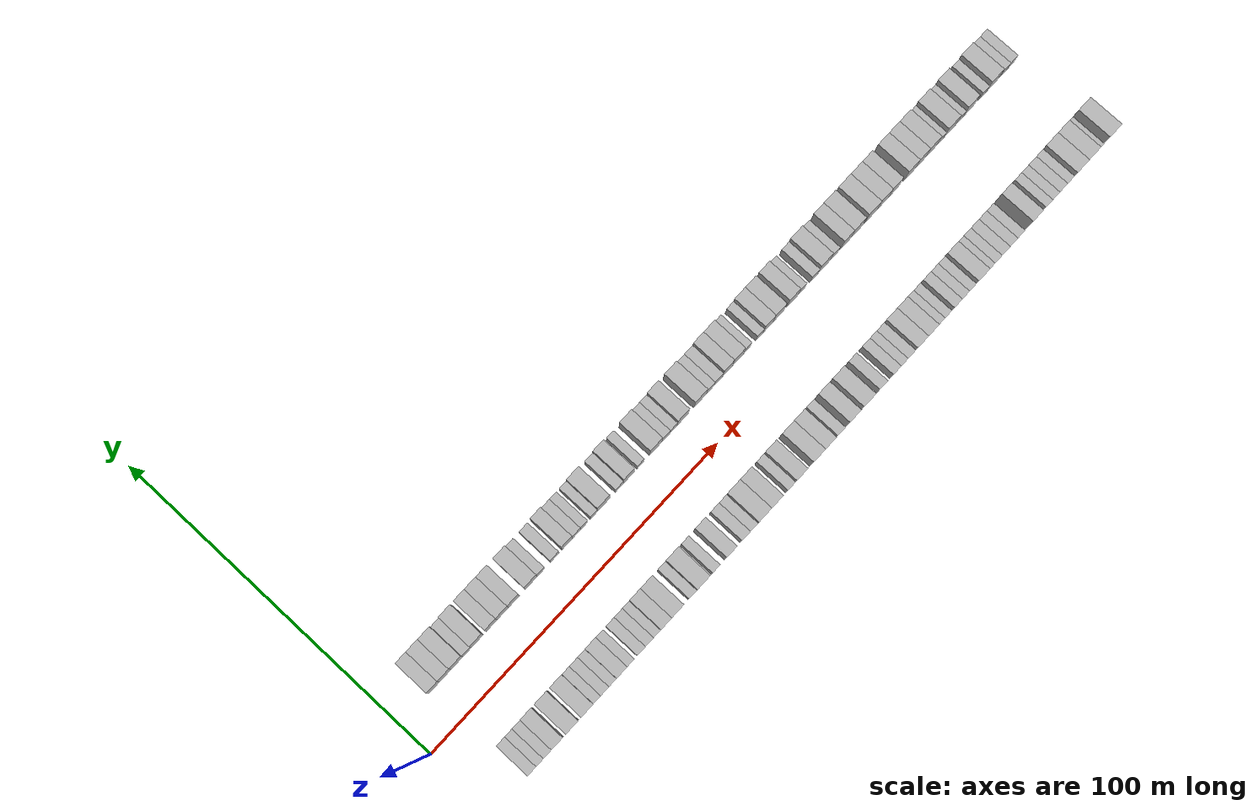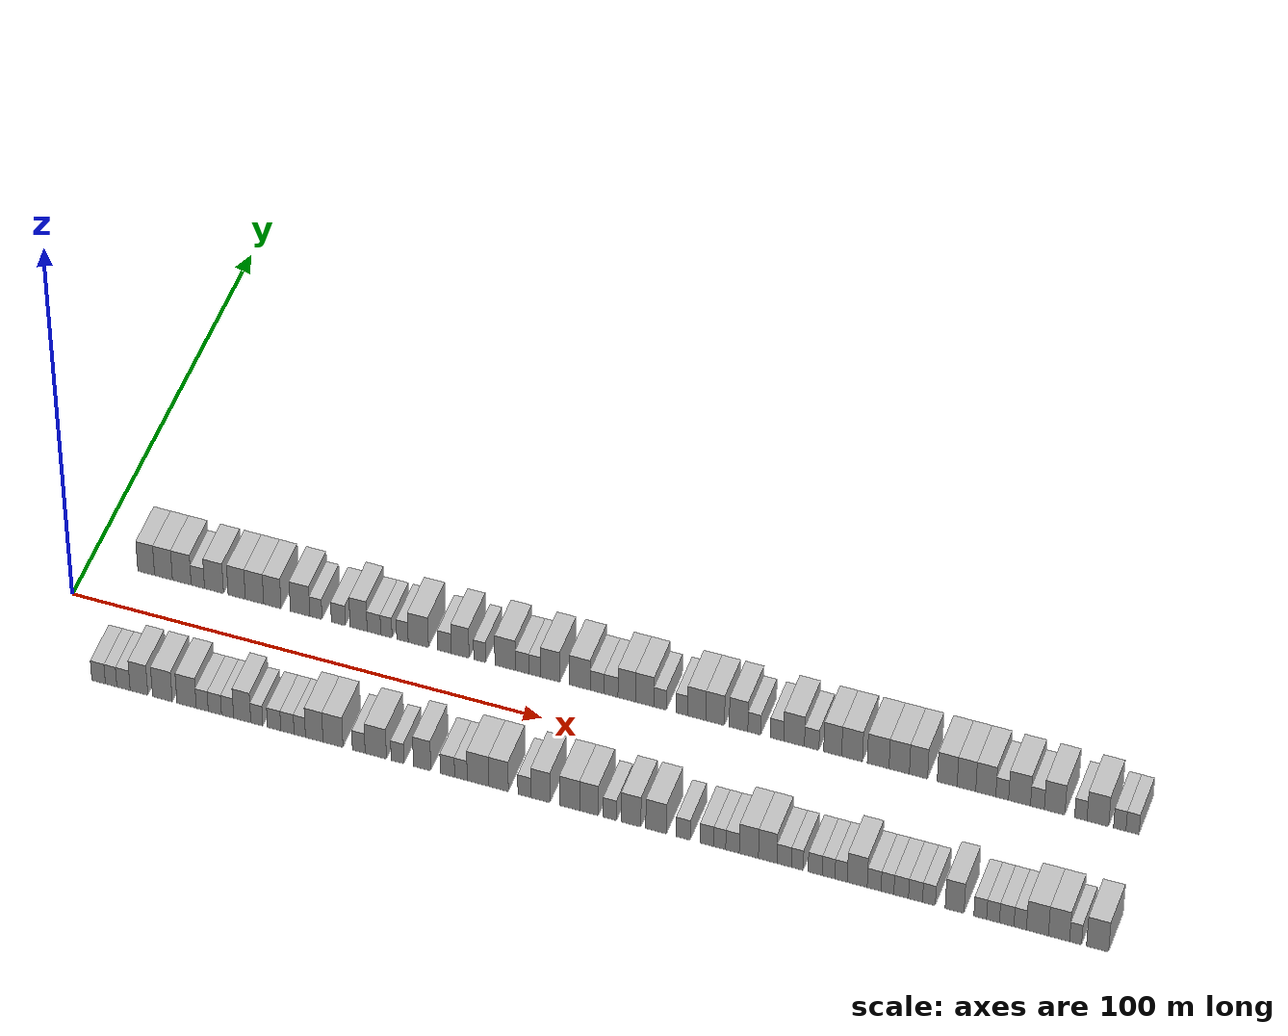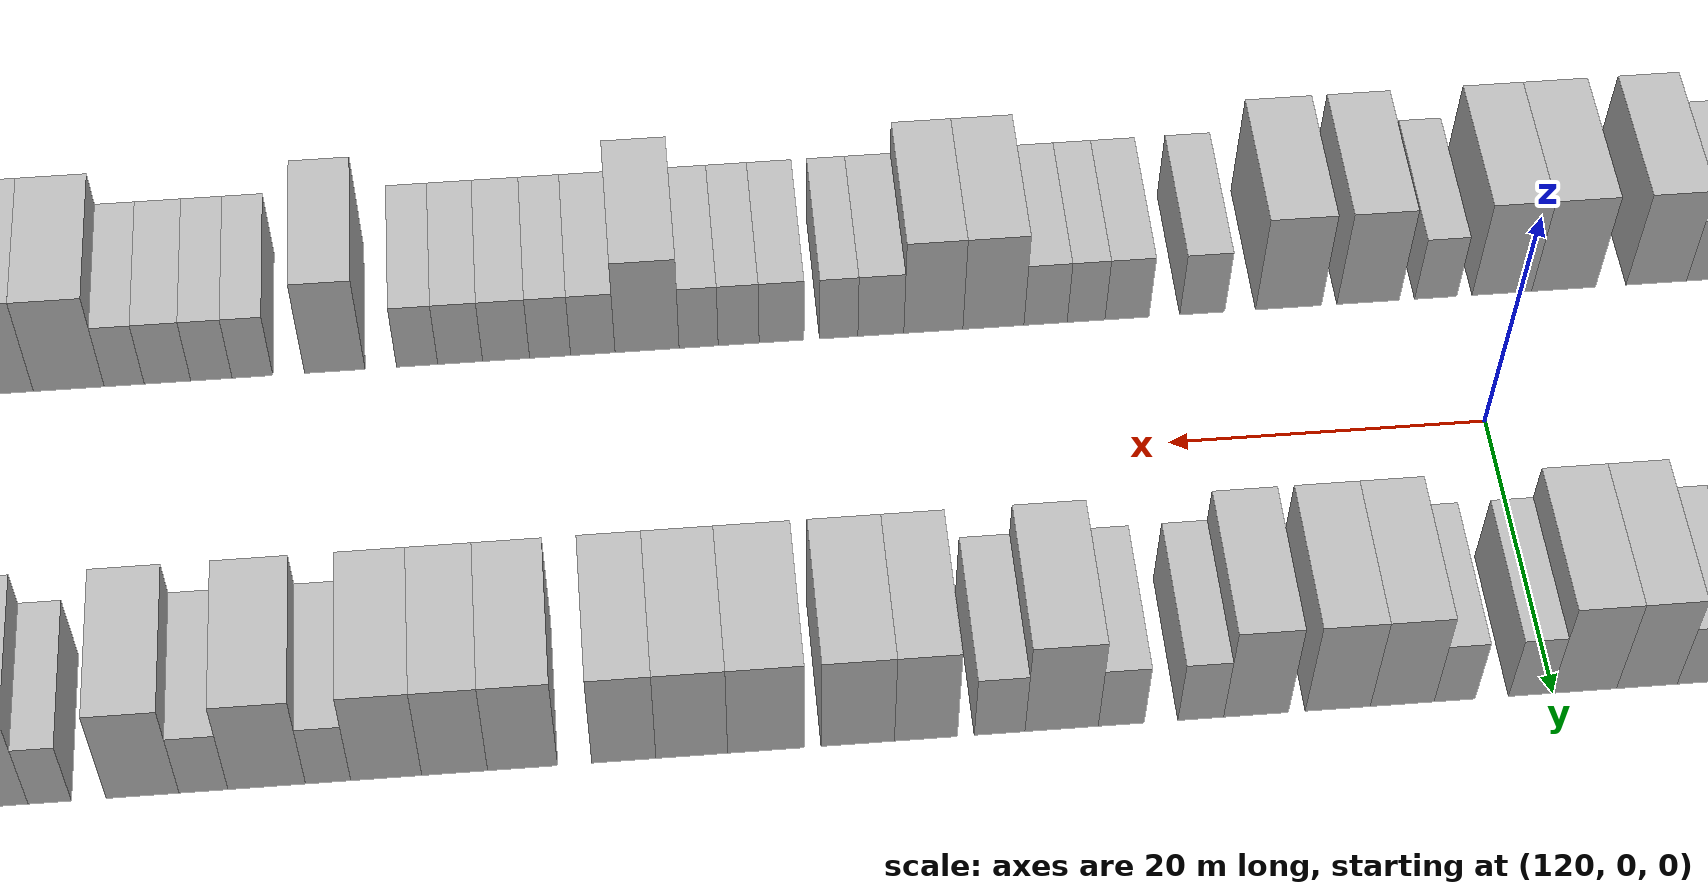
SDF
<sdf version="1.6">
 <world name="default">
  <scene>
   <sky><clouds><speed>12</speed></clouds></sky>
   <ambient>0.4 0.4 0.4 1</ambient>
   <background>0.7 0.7 0.7 1</background>
   <shadows>1</shadows>
  </scene>
  <gravity>0 0 -9.8066</gravity>
  <magnetic_field>6e-06 2.3e-05 -4.2e-05</magnetic_field>
  <physics default="0" name="default_physics" type="ode">
   <ode>
    <solver>
     <type>quick</type>
     <iters>10</iters>
     <sor>1.0</sor>
     <use_dynamic_moi_rescaling>0</use_dynamic_moi_rescaling>
    </solver>
    <constraints>
     <cfm>0</cfm>
     <erp>0.2</erp>
     <contact_max_correcting_vel>100</contact_max_correcting_vel>
     <contact_surface_layer>0.001</contact_surface_layer>
    </constraints>
   </ode>
   <max_step_size>0.004</max_step_size>
   <real_time_factor>1</real_time_factor>
   <real_time_update_rate>250</real_time_update_rate>
  </physics>
  <light name="sun" type="directional">
   <pose>0 0 10 0 0 0</pose>
   <diffuse>0.8 0.8 0.8 1</diffuse>
   <specular>0.2 0.2 0.2 1</specular>
   <attenuation>
    <range>1000</range>
    <constant>0.9</constant>
    <linear>0.01</linear>
    <quadratic>0.001</quadratic>
   </attenuation>
   <direction>-0.5 0.1 -0.9</direction>
  </light>
  <model name="building_1">
   <static>1</static>
   <pose>11.8060 15.0000 0 0.000000 0.000000 1.570796</pose>
   <link name="link">
    <pose>0 0 4.50 0 0 0</pose>
    <collision name="collision"><geometry><box><size>10.0000 3.6119 9.0000</size></box></geometry></collision>
    <visual name="visual">
     <cast_shadows>0</cast_shadows>
     <geometry><box><size>10.0000 3.6119 9.0000</size></box></geometry>
     <material>
      <script>
       <uri>model://HANNAS_wall/materials/scripts</uri>
       <uri>model://HANNAS_wall/materials/textures</uri>
       <name>vrc/HANNAS_wall</name>
      </script>
     </material>
    </visual>
   </link>
  </model>
  <model name="building_2">
   <static>1</static>
   <pose>15.5486 15.0000 0 0.000000 0.000000 1.570796</pose>
   <link name="link">
    <pose>0 0 4.50 0 0 0</pose>
    <collision name="collision"><geometry><box><size>10.0000 3.8733 9.0000</size></box></geometry></collision>
    <visual name="visual">
     <cast_shadows>0</cast_shadows>
     <geometry><box><size>10.0000 3.8733 9.0000</size></box></geometry>
     <material>
      <script>
       <uri>model://HANNAS_wall/materials/scripts</uri>
       <uri>model://HANNAS_wall/materials/textures</uri>
       <name>vrc/HANNAS_wall</name>
      </script>
     </material>
    </visual>
   </link>
  </model>
  <model name="building_3">
   <static>1</static>
   <pose>19.5123 15.0000 0 0.000000 0.000000 1.570796</pose>
   <link name="link">
    <pose>0 0 4.50 0 0 0</pose>
    <collision name="collision"><geometry><box><size>10.0000 4.0541 9.0000</size></box></geometry></collision>
    <visual name="visual">
     <cast_shadows>0</cast_shadows>
     <geometry><box><size>10.0000 4.0541 9.0000</size></box></geometry>
     <material>
      <script>
       <uri>model://HANNAS_wall/materials/scripts</uri>
       <uri>model://HANNAS_wall/materials/textures</uri>
       <name>vrc/HANNAS_wall</name>
      </script>
     </material>
    </visual>
   </link>
  </model>
  <model name="building_4">
   <static>1</static>
   <pose>22.9831 15.0000 0 0.000000 0.000000 1.570796</pose>
   <link name="link">
    <pose>0 0 3.00 0 0 0</pose>
    <collision name="collision"><geometry><box><size>10.0000 2.8875 6.0000</size></box></geometry></collision>
    <visual name="visual">
     <cast_shadows>0</cast_shadows>
     <geometry><box><size>10.0000 2.8875 6.0000</size></box></geometry>
     <material>
      <script>
       <uri>model://HANNAS_wall/materials/scripts</uri>
       <uri>model://HANNAS_wall/materials/textures</uri>
       <name>vrc/HANNAS_wall</name>
      </script>
     </material>
    </visual>
   </link>
  </model>
  <model name="building_5">
   <static>1</static>
   <pose>26.4760 15.0000 0 0.000000 0.000000 1.570796</pose>
   <link name="link">
    <pose>0 0 4.50 0 0 0</pose>
    <collision name="collision"><geometry><box><size>10.0000 4.0983 9.0000</size></box></geometry></collision>
    <visual name="visual">
     <cast_shadows>0</cast_shadows>
     <geometry><box><size>10.0000 4.0983 9.0000</size></box></geometry>
     <material>
      <script>
       <uri>model://HANNAS_wall/materials/scripts</uri>
       <uri>model://HANNAS_wall/materials/textures</uri>
       <name>vrc/HANNAS_wall</name>
      </script>
     </material>
    </visual>
   </link>
  </model>
  <model name="building_6">
   <static>1</static>
   <pose>31.3769 15.0000 0 0.000000 0.000000 1.570796</pose>
   <link name="link">
    <pose>0 0 4.50 0 0 0</pose>
    <collision name="collision"><geometry><box><size>10.0000 3.7035 9.0000</size></box></geometry></collision>
    <visual name="visual">
     <cast_shadows>0</cast_shadows>
     <geometry><box><size>10.0000 3.7035 9.0000</size></box></geometry>
     <material>
      <script>
       <uri>model://HANNAS_wall/materials/scripts</uri>
       <uri>model://HANNAS_wall/materials/textures</uri>
       <name>vrc/HANNAS_wall</name>
      </script>
     </material>
    </visual>
   </link>
  </model>
  <model name="building_7">
   <static>1</static>
   <pose>35.2094 15.0000 0 0.000000 0.000000 1.570796</pose>
   <link name="link">
    <pose>0 0 4.50 0 0 0</pose>
    <collision name="collision"><geometry><box><size>10.0000 3.9614 9.0000</size></box></geometry></collision>
    <visual name="visual">
     <cast_shadows>0</cast_shadows>
     <geometry><box><size>10.0000 3.9614 9.0000</size></box></geometry>
     <material>
      <script>
       <uri>model://HANNAS_wall/materials/scripts</uri>
       <uri>model://HANNAS_wall/materials/textures</uri>
       <name>vrc/HANNAS_wall</name>
      </script>
     </material>
    </visual>
   </link>
  </model>
  <model name="building_8">
   <static>1</static>
   <pose>39.0596 15.0000 0 0.000000 0.000000 1.570796</pose>
   <link name="link">
    <pose>0 0 4.50 0 0 0</pose>
    <collision name="collision"><geometry><box><size>10.0000 3.7391 9.0000</size></box></geometry></collision>
    <visual name="visual">
     <cast_shadows>0</cast_shadows>
     <geometry><box><size>10.0000 3.7391 9.0000</size></box></geometry>
     <material>
      <script>
       <uri>model://HANNAS_wall/materials/scripts</uri>
       <uri>model://HANNAS_wall/materials/textures</uri>
       <name>vrc/HANNAS_wall</name>
      </script>
     </material>
    </visual>
   </link>
  </model>
  <model name="building_9">
   <static>1</static>
   <pose>45.0208 15.0000 0 0.000000 0.000000 1.570796</pose>
   <link name="link">
    <pose>0 0 4.50 0 0 0</pose>
    <collision name="collision"><geometry><box><size>10.0000 4.1831 9.0000</size></box></geometry></collision>
    <visual name="visual">
     <cast_shadows>0</cast_shadows>
     <geometry><box><size>10.0000 4.1831 9.0000</size></box></geometry>
     <material>
      <script>
       <uri>model://HANNAS_wall/materials/scripts</uri>
       <uri>model://HANNAS_wall/materials/textures</uri>
       <name>vrc/HANNAS_wall</name>
      </script>
     </material>
    </visual>
   </link>
  </model>
  <model name="building_10">
   <static>1</static>
   <pose>48.4158 15.0000 0 0.000000 0.000000 1.570796</pose>
   <link name="link">
    <pose>0 0 3.00 0 0 0</pose>
    <collision name="collision"><geometry><box><size>10.0000 2.6068 6.0000</size></box></geometry></collision>
    <visual name="visual">
     <cast_shadows>0</cast_shadows>
     <geometry><box><size>10.0000 2.6068 6.0000</size></box></geometry>
     <material>
      <script>
       <uri>model://HANNAS_wall/materials/scripts</uri>
       <uri>model://HANNAS_wall/materials/textures</uri>
       <name>vrc/HANNAS_wall</name>
      </script>
     </material>
    </visual>
   </link>
  </model>
  <model name="building_11">
   <static>1</static>
   <pose>53.2167 15.0000 0 0.000000 0.000000 1.570796</pose>
   <link name="link">
    <pose>0 0 3.00 0 0 0</pose>
    <collision name="collision"><geometry><box><size>10.0000 2.9951 6.0000</size></box></geometry></collision>
    <visual name="visual">
     <cast_shadows>0</cast_shadows>
     <geometry><box><size>10.0000 2.9951 6.0000</size></box></geometry>
     <material>
      <script>
       <uri>model://HANNAS_wall/materials/scripts</uri>
       <uri>model://HANNAS_wall/materials/textures</uri>
       <name>vrc/HANNAS_wall</name>
      </script>
     </material>
    </visual>
   </link>
  </model>
  <model name="building_12">
   <static>1</static>
   <pose>57.5387 15.0000 0 0.000000 0.000000 1.570796</pose>
   <link name="link">
    <pose>0 0 4.50 0 0 0</pose>
    <collision name="collision"><geometry><box><size>10.0000 3.6490 9.0000</size></box></geometry></collision>
    <visual name="visual">
     <cast_shadows>0</cast_shadows>
     <geometry><box><size>10.0000 3.6490 9.0000</size></box></geometry>
     <material>
      <script>
       <uri>model://HANNAS_wall/materials/scripts</uri>
       <uri>model://HANNAS_wall/materials/textures</uri>
       <name>vrc/HANNAS_wall</name>
      </script>
     </material>
    </visual>
   </link>
  </model>
  <model name="building_13">
   <static>1</static>
   <pose>60.8177 15.0000 0 0.000000 0.000000 1.570796</pose>
   <link name="link">
    <pose>0 0 3.00 0 0 0</pose>
    <collision name="collision"><geometry><box><size>10.0000 2.9090 6.0000</size></box></geometry></collision>
    <visual name="visual">
     <cast_shadows>0</cast_shadows>
     <geometry><box><size>10.0000 2.9090 6.0000</size></box></geometry>
     <material>
      <script>
       <uri>model://HANNAS_wall/materials/scripts</uri>
       <uri>model://HANNAS_wall/materials/textures</uri>
       <name>vrc/HANNAS_wall</name>
      </script>
     </material>
    </visual>
   </link>
  </model>
  <model name="building_14">
   <static>1</static>
   <pose>63.4770 15.0000 0 0.000000 0.000000 1.570796</pose>
   <link name="link">
    <pose>0 0 3.00 0 0 0</pose>
    <collision name="collision"><geometry><box><size>10.0000 2.4096 6.0000</size></box></geometry></collision>
    <visual name="visual">
     <cast_shadows>0</cast_shadows>
     <geometry><box><size>10.0000 2.4096 6.0000</size></box></geometry>
     <material>
      <script>
       <uri>model://HANNAS_wall/materials/scripts</uri>
       <uri>model://HANNAS_wall/materials/textures</uri>
       <name>vrc/HANNAS_wall</name>
      </script>
     </material>
    </visual>
   </link>
  </model>
  <model name="building_15">
   <static>1</static>
   <pose>66.9053 15.0000 0 0.000000 0.000000 1.570796</pose>
   <link name="link">
    <pose>0 0 3.00 0 0 0</pose>
    <collision name="collision"><geometry><box><size>10.0000 2.4470 6.0000</size></box></geometry></collision>
    <visual name="visual">
     <cast_shadows>0</cast_shadows>
     <geometry><box><size>10.0000 2.4470 6.0000</size></box></geometry>
     <material>
      <script>
       <uri>model://HANNAS_wall/materials/scripts</uri>
       <uri>model://HANNAS_wall/materials/textures</uri>
       <name>vrc/HANNAS_wall</name>
      </script>
     </material>
    </visual>
   </link>
  </model>
  <model name="building_16">
   <static>1</static>
   <pose>70.2902 15.0000 0 0.000000 0.000000 1.570796</pose>
   <link name="link">
    <pose>0 0 4.50 0 0 0</pose>
    <collision name="collision"><geometry><box><size>10.0000 4.3228 9.0000</size></box></geometry></collision>
    <visual name="visual">
     <cast_shadows>0</cast_shadows>
     <geometry><box><size>10.0000 4.3228 9.0000</size></box></geometry>
     <material>
      <script>
       <uri>model://HANNAS_wall/materials/scripts</uri>
       <uri>model://HANNAS_wall/materials/textures</uri>
       <name>vrc/HANNAS_wall</name>
      </script>
     </material>
    </visual>
   </link>
  </model>
  <model name="building_17">
   <static>1</static>
   <pose>75.8866 15.0000 0 0.000000 0.000000 1.570796</pose>
   <link name="link">
    <pose>0 0 3.00 0 0 0</pose>
    <collision name="collision"><geometry><box><size>10.0000 2.8701 6.0000</size></box></geometry></collision>
    <visual name="visual">
     <cast_shadows>0</cast_shadows>
     <geometry><box><size>10.0000 2.8701 6.0000</size></box></geometry>
     <material>
      <script>
       <uri>model://HANNAS_wall/materials/scripts</uri>
       <uri>model://HANNAS_wall/materials/textures</uri>
       <name>vrc/HANNAS_wall</name>
      </script>
     </material>
    </visual>
   </link>
  </model>
  <model name="building_18">
   <static>1</static>
   <pose>79.2001 15.0000 0 0.000000 0.000000 1.570796</pose>
   <link name="link">
    <pose>0 0 4.50 0 0 0</pose>
    <collision name="collision"><geometry><box><size>10.0000 3.7569 9.0000</size></box></geometry></collision>
    <visual name="visual">
     <cast_shadows>0</cast_shadows>
     <geometry><box><size>10.0000 3.7569 9.0000</size></box></geometry>
     <material>
      <script>
       <uri>model://HANNAS_wall/materials/scripts</uri>
       <uri>model://HANNAS_wall/materials/textures</uri>
       <name>vrc/HANNAS_wall</name>
      </script>
     </material>
    </visual>
   </link>
  </model>
  <model name="building_19">
   <static>1</static>
   <pose>83.3253 15.0000 0 0.000000 0.000000 1.570796</pose>
   <link name="link">
    <pose>0 0 3.00 0 0 0</pose>
    <collision name="collision"><geometry><box><size>10.0000 2.4935 6.0000</size></box></geometry></collision>
    <visual name="visual">
     <cast_shadows>0</cast_shadows>
     <geometry><box><size>10.0000 2.4935 6.0000</size></box></geometry>
     <material>
      <script>
       <uri>model://HANNAS_wall/materials/scripts</uri>
       <uri>model://HANNAS_wall/materials/textures</uri>
       <name>vrc/HANNAS_wall</name>
      </script>
     </material>
    </visual>
   </link>
  </model>
  <model name="building_20">
   <static>1</static>
   <pose>88.7367 15.0000 0 0.000000 0.000000 1.570796</pose>
   <link name="link">
    <pose>0 0 4.50 0 0 0</pose>
    <collision name="collision"><geometry><box><size>10.0000 4.3294 9.0000</size></box></geometry></collision>
    <visual name="visual">
     <cast_shadows>0</cast_shadows>
     <geometry><box><size>10.0000 4.3294 9.0000</size></box></geometry>
     <material>
      <script>
       <uri>model://HANNAS_wall/materials/scripts</uri>
       <uri>model://HANNAS_wall/materials/textures</uri>
       <name>vrc/HANNAS_wall</name>
      </script>
     </material>
    </visual>
   </link>
  </model>
  <model name="building_21">
   <static>1</static>
   <pose>92.3291 15.0000 0 0.000000 0.000000 1.570796</pose>
   <link name="link">
    <pose>0 0 3.00 0 0 0</pose>
    <collision name="collision"><geometry><box><size>10.0000 2.8554 6.0000</size></box></geometry></collision>
    <visual name="visual">
     <cast_shadows>0</cast_shadows>
     <geometry><box><size>10.0000 2.8554 6.0000</size></box></geometry>
     <material>
      <script>
       <uri>model://HANNAS_wall/materials/scripts</uri>
       <uri>model://HANNAS_wall/materials/textures</uri>
       <name>vrc/HANNAS_wall</name>
      </script>
     </material>
    </visual>
   </link>
  </model>
  <model name="building_22">
   <static>1</static>
   <pose>95.0133 15.0000 0 0.000000 0.000000 1.570796</pose>
   <link name="link">
    <pose>0 0 3.00 0 0 0</pose>
    <collision name="collision"><geometry><box><size>10.0000 2.5129 6.0000</size></box></geometry></collision>
    <visual name="visual">
     <cast_shadows>0</cast_shadows>
     <geometry><box><size>10.0000 2.5129 6.0000</size></box></geometry>
     <material>
      <script>
       <uri>model://HANNAS_wall/materials/scripts</uri>
       <uri>model://HANNAS_wall/materials/textures</uri>
       <name>vrc/HANNAS_wall</name>
      </script>
     </material>
    </visual>
   </link>
  </model>
  <model name="building_23">
   <static>1</static>
   <pose>98.2925 15.0000 0 0.000000 0.000000 1.570796</pose>
   <link name="link">
    <pose>0 0 4.50 0 0 0</pose>
    <collision name="collision"><geometry><box><size>10.0000 4.0456 9.0000</size></box></geometry></collision>
    <visual name="visual">
     <cast_shadows>0</cast_shadows>
     <geometry><box><size>10.0000 4.0456 9.0000</size></box></geometry>
     <material>
      <script>
       <uri>model://HANNAS_wall/materials/scripts</uri>
       <uri>model://HANNAS_wall/materials/textures</uri>
       <name>vrc/HANNAS_wall</name>
      </script>
     </material>
    </visual>
   </link>
  </model>
  <model name="building_24">
   <static>1</static>
   <pose>104.5154 15.0000 0 0.000000 0.000000 1.570796</pose>
   <link name="link">
    <pose>0 0 4.50 0 0 0</pose>
    <collision name="collision"><geometry><box><size>10.0000 4.4003 9.0000</size></box></geometry></collision>
    <visual name="visual">
     <cast_shadows>0</cast_shadows>
     <geometry><box><size>10.0000 4.4003 9.0000</size></box></geometry>
     <material>
      <script>
       <uri>model://HANNAS_wall/materials/scripts</uri>
       <uri>model://HANNAS_wall/materials/textures</uri>
       <name>vrc/HANNAS_wall</name>
      </script>
     </material>
    </visual>
   </link>
  </model>
  <model name="building_25">
   <static>1</static>
   <pose>108.1630 15.0000 0 0.000000 0.000000 1.570796</pose>
   <link name="link">
    <pose>0 0 3.00 0 0 0</pose>
    <collision name="collision"><geometry><box><size>10.0000 2.8949 6.0000</size></box></geometry></collision>
    <visual name="visual">
     <cast_shadows>0</cast_shadows>
     <geometry><box><size>10.0000 2.8949 6.0000</size></box></geometry>
     <material>
      <script>
       <uri>model://HANNAS_wall/materials/scripts</uri>
       <uri>model://HANNAS_wall/materials/textures</uri>
       <name>vrc/HANNAS_wall</name>
      </script>
     </material>
    </visual>
   </link>
  </model>
  <model name="building_26">
   <static>1</static>
   <pose>111.0786 15.0000 0 0.000000 0.000000 1.570796</pose>
   <link name="link">
    <pose>0 0 3.00 0 0 0</pose>
    <collision name="collision"><geometry><box><size>10.0000 2.9363 6.0000</size></box></geometry></collision>
    <visual name="visual">
     <cast_shadows>0</cast_shadows>
     <geometry><box><size>10.0000 2.9363 6.0000</size></box></geometry>
     <material>
      <script>
       <uri>model://HANNAS_wall/materials/scripts</uri>
       <uri>model://HANNAS_wall/materials/textures</uri>
       <name>vrc/HANNAS_wall</name>
      </script>
     </material>
    </visual>
   </link>
  </model>
  <model name="building_27">
   <static>1</static>
   <pose>114.3755 15.0000 0 0.000000 0.000000 1.570796</pose>
   <link name="link">
    <pose>0 0 4.50 0 0 0</pose>
    <collision name="collision"><geometry><box><size>10.0000 3.6575 9.0000</size></box></geometry></collision>
    <visual name="visual">
     <cast_shadows>0</cast_shadows>
     <geometry><box><size>10.0000 3.6575 9.0000</size></box></geometry>
     <material>
      <script>
       <uri>model://HANNAS_wall/materials/scripts</uri>
       <uri>model://HANNAS_wall/materials/textures</uri>
       <name>vrc/HANNAS_wall</name>
      </script>
     </material>
    </visual>
   </link>
  </model>
  <model name="building_28">
   <static>1</static>
   <pose>118.1713 15.0000 0 0.000000 0.000000 1.570796</pose>
   <link name="link">
    <pose>0 0 4.50 0 0 0</pose>
    <collision name="collision"><geometry><box><size>10.0000 3.9341 9.0000</size></box></geometry></collision>
    <visual name="visual">
     <cast_shadows>0</cast_shadows>
     <geometry><box><size>10.0000 3.9341 9.0000</size></box></geometry>
     <material>
      <script>
       <uri>model://HANNAS_wall/materials/scripts</uri>
       <uri>model://HANNAS_wall/materials/textures</uri>
       <name>vrc/HANNAS_wall</name>
      </script>
     </material>
    </visual>
   </link>
  </model>
  <model name="building_29">
   <static>1</static>
   <pose>121.4217 15.0000 0 0.000000 0.000000 1.570796</pose>
   <link name="link">
    <pose>0 0 3.00 0 0 0</pose>
    <collision name="collision"><geometry><box><size>10.0000 2.5667 6.0000</size></box></geometry></collision>
    <visual name="visual">
     <cast_shadows>0</cast_shadows>
     <geometry><box><size>10.0000 2.5667 6.0000</size></box></geometry>
     <material>
      <script>
       <uri>model://HANNAS_wall/materials/scripts</uri>
       <uri>model://HANNAS_wall/materials/textures</uri>
       <name>vrc/HANNAS_wall</name>
      </script>
     </material>
    </visual>
   </link>
  </model>
  <model name="building_30">
   <static>1</static>
   <pose>125.9357 15.0000 0 0.000000 0.000000 1.570796</pose>
   <link name="link">
    <pose>0 0 3.00 0 0 0</pose>
    <collision name="collision"><geometry><box><size>10.0000 2.4612 6.0000</size></box></geometry></collision>
    <visual name="visual">
     <cast_shadows>0</cast_shadows>
     <geometry><box><size>10.0000 2.4612 6.0000</size></box></geometry>
     <material>
      <script>
       <uri>model://HANNAS_wall/materials/scripts</uri>
       <uri>model://HANNAS_wall/materials/textures</uri>
       <name>vrc/HANNAS_wall</name>
      </script>
     </material>
    </visual>
   </link>
  </model>
  <model name="building_31">
   <static>1</static>
   <pose>129.0759 15.0000 0 0.000000 0.000000 1.570796</pose>
   <link name="link">
    <pose>0 0 4.50 0 0 0</pose>
    <collision name="collision"><geometry><box><size>10.0000 3.8192 9.0000</size></box></geometry></collision>
    <visual name="visual">
     <cast_shadows>0</cast_shadows>
     <geometry><box><size>10.0000 3.8192 9.0000</size></box></geometry>
     <material>
      <script>
       <uri>model://HANNAS_wall/materials/scripts</uri>
       <uri>model://HANNAS_wall/materials/textures</uri>
       <name>vrc/HANNAS_wall</name>
      </script>
     </material>
    </visual>
   </link>
  </model>
  <model name="building_32">
   <static>1</static>
   <pose>132.9292 15.0000 0 0.000000 0.000000 1.570796</pose>
   <link name="link">
    <pose>0 0 4.50 0 0 0</pose>
    <collision name="collision"><geometry><box><size>10.0000 3.8874 9.0000</size></box></geometry></collision>
    <visual name="visual">
     <cast_shadows>0</cast_shadows>
     <geometry><box><size>10.0000 3.8874 9.0000</size></box></geometry>
     <material>
      <script>
       <uri>model://HANNAS_wall/materials/scripts</uri>
       <uri>model://HANNAS_wall/materials/textures</uri>
       <name>vrc/HANNAS_wall</name>
      </script>
     </material>
    </visual>
   </link>
  </model>
  <model name="building_33">
   <static>1</static>
   <pose>137.8055 15.0000 0 0.000000 0.000000 1.570796</pose>
   <link name="link">
    <pose>0 0 4.50 0 0 0</pose>
    <collision name="collision"><geometry><box><size>10.0000 3.8652 9.0000</size></box></geometry></collision>
    <visual name="visual">
     <cast_shadows>0</cast_shadows>
     <geometry><box><size>10.0000 3.8652 9.0000</size></box></geometry>
     <material>
      <script>
       <uri>model://HANNAS_wall/materials/scripts</uri>
       <uri>model://HANNAS_wall/materials/textures</uri>
       <name>vrc/HANNAS_wall</name>
      </script>
     </material>
    </visual>
   </link>
  </model>
  <model name="building_34">
   <static>1</static>
   <pose>141.0988 15.0000 0 0.000000 0.000000 1.570796</pose>
   <link name="link">
    <pose>0 0 3.00 0 0 0</pose>
    <collision name="collision"><geometry><box><size>10.0000 2.7214 6.0000</size></box></geometry></collision>
    <visual name="visual">
     <cast_shadows>0</cast_shadows>
     <geometry><box><size>10.0000 2.7214 6.0000</size></box></geometry>
     <material>
      <script>
       <uri>model://HANNAS_wall/materials/scripts</uri>
       <uri>model://HANNAS_wall/materials/textures</uri>
       <name>vrc/HANNAS_wall</name>
      </script>
     </material>
    </visual>
   </link>
  </model>
  <model name="building_35">
   <static>1</static>
   <pose>145.8240 15.0000 0 0.000000 0.000000 1.570796</pose>
   <link name="link">
    <pose>0 0 3.00 0 0 0</pose>
    <collision name="collision"><geometry><box><size>10.0000 2.7289 6.0000</size></box></geometry></collision>
    <visual name="visual">
     <cast_shadows>0</cast_shadows>
     <geometry><box><size>10.0000 2.7289 6.0000</size></box></geometry>
     <material>
      <script>
       <uri>model://HANNAS_wall/materials/scripts</uri>
       <uri>model://HANNAS_wall/materials/textures</uri>
       <name>vrc/HANNAS_wall</name>
      </script>
     </material>
    </visual>
   </link>
  </model>
  <model name="building_36">
   <static>1</static>
   <pose>149.3611 15.0000 0 0.000000 0.000000 1.570796</pose>
   <link name="link">
    <pose>0 0 4.50 0 0 0</pose>
    <collision name="collision"><geometry><box><size>10.0000 4.3454 9.0000</size></box></geometry></collision>
    <visual name="visual">
     <cast_shadows>0</cast_shadows>
     <geometry><box><size>10.0000 4.3454 9.0000</size></box></geometry>
     <material>
      <script>
       <uri>model://HANNAS_wall/materials/scripts</uri>
       <uri>model://HANNAS_wall/materials/textures</uri>
       <name>vrc/HANNAS_wall</name>
      </script>
     </material>
    </visual>
   </link>
  </model>
  <model name="building_37">
   <static>1</static>
   <pose>153.0323 15.0000 0 0.000000 0.000000 1.570796</pose>
   <link name="link">
    <pose>0 0 3.00 0 0 0</pose>
    <collision name="collision"><geometry><box><size>10.0000 2.9968 6.0000</size></box></geometry></collision>
    <visual name="visual">
     <cast_shadows>0</cast_shadows>
     <geometry><box><size>10.0000 2.9968 6.0000</size></box></geometry>
     <material>
      <script>
       <uri>model://HANNAS_wall/materials/scripts</uri>
       <uri>model://HANNAS_wall/materials/textures</uri>
       <name>vrc/HANNAS_wall</name>
      </script>
     </material>
    </visual>
   </link>
  </model>
  <model name="building_38">
   <static>1</static>
   <pose>157.3889 15.0000 0 0.000000 0.000000 1.570796</pose>
   <link name="link">
    <pose>0 0 4.50 0 0 0</pose>
    <collision name="collision"><geometry><box><size>10.0000 3.7164 9.0000</size></box></geometry></collision>
    <visual name="visual">
     <cast_shadows>0</cast_shadows>
     <geometry><box><size>10.0000 3.7164 9.0000</size></box></geometry>
     <material>
      <script>
       <uri>model://HANNAS_wall/materials/scripts</uri>
       <uri>model://HANNAS_wall/materials/textures</uri>
       <name>vrc/HANNAS_wall</name>
      </script>
     </material>
    </visual>
   </link>
  </model>
  <model name="building_39">
   <static>1</static>
   <pose>161.4057 15.0000 0 0.000000 0.000000 1.570796</pose>
   <link name="link">
    <pose>0 0 4.50 0 0 0</pose>
    <collision name="collision"><geometry><box><size>10.0000 4.3173 9.0000</size></box></geometry></collision>
    <visual name="visual">
     <cast_shadows>0</cast_shadows>
     <geometry><box><size>10.0000 4.3173 9.0000</size></box></geometry>
     <material>
      <script>
       <uri>model://HANNAS_wall/materials/scripts</uri>
       <uri>model://HANNAS_wall/materials/textures</uri>
       <name>vrc/HANNAS_wall</name>
      </script>
     </material>
    </visual>
   </link>
  </model>
  <model name="building_40">
   <static>1</static>
   <pose>166.8113 15.0000 0 0.000000 0.000000 1.570796</pose>
   <link name="link">
    <pose>0 0 4.50 0 0 0</pose>
    <collision name="collision"><geometry><box><size>10.0000 4.4940 9.0000</size></box></geometry></collision>
    <visual name="visual">
     <cast_shadows>0</cast_shadows>
     <geometry><box><size>10.0000 4.4940 9.0000</size></box></geometry>
     <material>
      <script>
       <uri>model://HANNAS_wall/materials/scripts</uri>
       <uri>model://HANNAS_wall/materials/textures</uri>
       <name>vrc/HANNAS_wall</name>
      </script>
     </material>
    </visual>
   </link>
  </model>
  <model name="building_41">
   <static>1</static>
   <pose>171.1600 15.0000 0 0.000000 0.000000 1.570796</pose>
   <link name="link">
    <pose>0 0 4.50 0 0 0</pose>
    <collision name="collision"><geometry><box><size>10.0000 4.2035 9.0000</size></box></geometry></collision>
    <visual name="visual">
     <cast_shadows>0</cast_shadows>
     <geometry><box><size>10.0000 4.2035 9.0000</size></box></geometry>
     <material>
      <script>
       <uri>model://HANNAS_wall/materials/scripts</uri>
       <uri>model://HANNAS_wall/materials/textures</uri>
       <name>vrc/HANNAS_wall</name>
      </script>
     </material>
    </visual>
   </link>
  </model>
  <model name="building_42">
   <static>1</static>
   <pose>175.1367 15.0000 0 0.000000 0.000000 1.570796</pose>
   <link name="link">
    <pose>0 0 4.50 0 0 0</pose>
    <collision name="collision"><geometry><box><size>10.0000 3.7498 9.0000</size></box></geometry></collision>
    <visual name="visual">
     <cast_shadows>0</cast_shadows>
     <geometry><box><size>10.0000 3.7498 9.0000</size></box></geometry>
     <material>
      <script>
       <uri>model://HANNAS_wall/materials/scripts</uri>
       <uri>model://HANNAS_wall/materials/textures</uri>
       <name>vrc/HANNAS_wall</name>
      </script>
     </material>
    </visual>
   </link>
  </model>
  <model name="building_43">
   <static>1</static>
   <pose>181.0527 15.0000 0 0.000000 0.000000 1.570796</pose>
   <link name="link">
    <pose>0 0 4.50 0 0 0</pose>
    <collision name="collision"><geometry><box><size>10.0000 4.0822 9.0000</size></box></geometry></collision>
    <visual name="visual">
     <cast_shadows>0</cast_shadows>
     <geometry><box><size>10.0000 4.0822 9.0000</size></box></geometry>
     <material>
      <script>
       <uri>model://HANNAS_wall/materials/scripts</uri>
       <uri>model://HANNAS_wall/materials/textures</uri>
       <name>vrc/HANNAS_wall</name>
      </script>
     </material>
    </visual>
   </link>
  </model>
  <model name="building_44">
   <static>1</static>
   <pose>185.0109 15.0000 0 0.000000 0.000000 1.570796</pose>
   <link name="link">
    <pose>0 0 4.50 0 0 0</pose>
    <collision name="collision"><geometry><box><size>10.0000 3.8343 9.0000</size></box></geometry></collision>
    <visual name="visual">
     <cast_shadows>0</cast_shadows>
     <geometry><box><size>10.0000 3.8343 9.0000</size></box></geometry>
     <material>
      <script>
       <uri>model://HANNAS_wall/materials/scripts</uri>
       <uri>model://HANNAS_wall/materials/textures</uri>
       <name>vrc/HANNAS_wall</name>
      </script>
     </material>
    </visual>
   </link>
  </model>
  <model name="building_45">
   <static>1</static>
   <pose>188.9912 15.0000 0 0.000000 0.000000 1.570796</pose>
   <link name="link">
    <pose>0 0 4.50 0 0 0</pose>
    <collision name="collision"><geometry><box><size>10.0000 4.1263 9.0000</size></box></geometry></collision>
    <visual name="visual">
     <cast_shadows>0</cast_shadows>
     <geometry><box><size>10.0000 4.1263 9.0000</size></box></geometry>
     <material>
      <script>
       <uri>model://HANNAS_wall/materials/scripts</uri>
       <uri>model://HANNAS_wall/materials/textures</uri>
       <name>vrc/HANNAS_wall</name>
      </script>
     </material>
    </visual>
   </link>
  </model>
  <model name="building_46">
   <static>1</static>
   <pose>192.3655 15.0000 0 0.000000 0.000000 1.570796</pose>
   <link name="link">
    <pose>0 0 3.00 0 0 0</pose>
    <collision name="collision"><geometry><box><size>10.0000 2.6222 6.0000</size></box></geometry></collision>
    <visual name="visual">
     <cast_shadows>0</cast_shadows>
     <geometry><box><size>10.0000 2.6222 6.0000</size></box></geometry>
     <material>
      <script>
       <uri>model://HANNAS_wall/materials/scripts</uri>
       <uri>model://HANNAS_wall/materials/textures</uri>
       <name>vrc/HANNAS_wall</name>
      </script>
     </material>
    </visual>
   </link>
  </model>
  <model name="building_47">
   <static>1</static>
   <pose>195.9223 15.0000 0 0.000000 0.000000 1.570796</pose>
   <link name="link">
    <pose>0 0 4.50 0 0 0</pose>
    <collision name="collision"><geometry><box><size>10.0000 4.4914 9.0000</size></box></geometry></collision>
    <visual name="visual">
     <cast_shadows>0</cast_shadows>
     <geometry><box><size>10.0000 4.4914 9.0000</size></box></geometry>
     <material>
      <script>
       <uri>model://HANNAS_wall/materials/scripts</uri>
       <uri>model://HANNAS_wall/materials/textures</uri>
       <name>vrc/HANNAS_wall</name>
      </script>
     </material>
    </visual>
   </link>
  </model>
  <model name="building_48">
   <static>1</static>
   <pose>199.5818 15.0000 0 0.000000 0.000000 1.570796</pose>
   <link name="link">
    <pose>0 0 3.00 0 0 0</pose>
    <collision name="collision"><geometry><box><size>10.0000 2.8277 6.0000</size></box></geometry></collision>
    <visual name="visual">
     <cast_shadows>0</cast_shadows>
     <geometry><box><size>10.0000 2.8277 6.0000</size></box></geometry>
     <material>
      <script>
       <uri>model://HANNAS_wall/materials/scripts</uri>
       <uri>model://HANNAS_wall/materials/textures</uri>
       <name>vrc/HANNAS_wall</name>
      </script>
     </material>
    </visual>
   </link>
  </model>
  <model name="building_49">
   <static>1</static>
   <pose>203.1002 15.0000 0 0.000000 0.000000 1.570796</pose>
   <link name="link">
    <pose>0 0 4.50 0 0 0</pose>
    <collision name="collision"><geometry><box><size>10.0000 4.2091 9.0000</size></box></geometry></collision>
    <visual name="visual">
     <cast_shadows>0</cast_shadows>
     <geometry><box><size>10.0000 4.2091 9.0000</size></box></geometry>
     <material>
      <script>
       <uri>model://HANNAS_wall/materials/scripts</uri>
       <uri>model://HANNAS_wall/materials/textures</uri>
       <name>vrc/HANNAS_wall</name>
      </script>
     </material>
    </visual>
   </link>
  </model>
  <model name="building_50">
   <static>1</static>
   <pose>208.4512 15.0000 0 0.000000 0.000000 1.570796</pose>
   <link name="link">
    <pose>0 0 3.00 0 0 0</pose>
    <collision name="collision"><geometry><box><size>10.0000 2.4929 6.0000</size></box></geometry></collision>
    <visual name="visual">
     <cast_shadows>0</cast_shadows>
     <geometry><box><size>10.0000 2.4929 6.0000</size></box></geometry>
     <material>
      <script>
       <uri>model://HANNAS_wall/materials/scripts</uri>
       <uri>model://HANNAS_wall/materials/textures</uri>
       <name>vrc/HANNAS_wall</name>
      </script>
     </material>
    </visual>
   </link>
  </model>
  <model name="building_51">
   <static>1</static>
   <pose>211.9176 15.0000 0 0.000000 0.000000 1.570796</pose>
   <link name="link">
    <pose>0 0 4.50 0 0 0</pose>
    <collision name="collision"><geometry><box><size>10.0000 4.4398 9.0000</size></box></geometry></collision>
    <visual name="visual">
     <cast_shadows>0</cast_shadows>
     <geometry><box><size>10.0000 4.4398 9.0000</size></box></geometry>
     <material>
      <script>
       <uri>model://HANNAS_wall/materials/scripts</uri>
       <uri>model://HANNAS_wall/materials/textures</uri>
       <name>vrc/HANNAS_wall</name>
      </script>
     </material>
    </visual>
   </link>
  </model>
  <model name="building_52">
   <static>1</static>
   <pose>216.3968 15.0000 0 0.000000 0.000000 1.570796</pose>
   <link name="link">
    <pose>0 0 3.00 0 0 0</pose>
    <collision name="collision"><geometry><box><size>10.0000 2.5186 6.0000</size></box></geometry></collision>
    <visual name="visual">
     <cast_shadows>0</cast_shadows>
     <geometry><box><size>10.0000 2.5186 6.0000</size></box></geometry>
     <material>
      <script>
       <uri>model://HANNAS_wall/materials/scripts</uri>
       <uri>model://HANNAS_wall/materials/textures</uri>
       <name>vrc/HANNAS_wall</name>
      </script>
     </material>
    </visual>
   </link>
  </model>
  <model name="building_53">
   <static>1</static>
   <pose>218.9856 15.0000 0 0.000000 0.000000 1.570796</pose>
   <link name="link">
    <pose>0 0 3.00 0 0 0</pose>
    <collision name="collision"><geometry><box><size>10.0000 2.6590 6.0000</size></box></geometry></collision>
    <visual name="visual">
     <cast_shadows>0</cast_shadows>
     <geometry><box><size>10.0000 2.6590 6.0000</size></box></geometry>
     <material>
      <script>
       <uri>model://HANNAS_wall/materials/scripts</uri>
       <uri>model://HANNAS_wall/materials/textures</uri>
       <name>vrc/HANNAS_wall</name>
      </script>
     </material>
    </visual>
   </link>
  </model>
  <model name="building_54">
   <static>1</static>
   <pose>13.4438 -15.0000 0 0.000000 0.000000 1.570796</pose>
   <link name="link">
    <pose>0 0 3.00 0 0 0</pose>
    <collision name="collision"><geometry><box><size>10.0000 2.8877 6.0000</size></box></geometry></collision>
    <visual name="visual">
     <cast_shadows>0</cast_shadows>
     <geometry><box><size>10.0000 2.8877 6.0000</size></box></geometry>
     <material>
      <script>
       <uri>model://HANNAS_wall/materials/scripts</uri>
       <uri>model://HANNAS_wall/materials/textures</uri>
       <name>vrc/HANNAS_wall</name>
      </script>
     </material>
    </visual>
   </link>
  </model>
  <model name="building_55">
   <static>1</static>
   <pose>16.1163 -15.0000 0 0.000000 0.000000 1.570796</pose>
   <link name="link">
    <pose>0 0 3.00 0 0 0</pose>
    <collision name="collision"><geometry><box><size>10.0000 2.4572 6.0000</size></box></geometry></collision>
    <visual name="visual">
     <cast_shadows>0</cast_shadows>
     <geometry><box><size>10.0000 2.4572 6.0000</size></box></geometry>
     <material>
      <script>
       <uri>model://HANNAS_wall/materials/scripts</uri>
       <uri>model://HANNAS_wall/materials/textures</uri>
       <name>vrc/HANNAS_wall</name>
      </script>
     </material>
    </visual>
   </link>
  </model>
  <model name="building_56">
   <static>1</static>
   <pose>18.7672 -15.0000 0 0.000000 0.000000 1.570796</pose>
   <link name="link">
    <pose>0 0 3.00 0 0 0</pose>
    <collision name="collision"><geometry><box><size>10.0000 2.8445 6.0000</size></box></geometry></collision>
    <visual name="visual">
     <cast_shadows>0</cast_shadows>
     <geometry><box><size>10.0000 2.8445 6.0000</size></box></geometry>
     <material>
      <script>
       <uri>model://HANNAS_wall/materials/scripts</uri>
       <uri>model://HANNAS_wall/materials/textures</uri>
       <name>vrc/HANNAS_wall</name>
      </script>
     </material>
    </visual>
   </link>
  </model>
  <model name="building_57">
   <static>1</static>
   <pose>22.0871 -15.0000 0 0.000000 0.000000 1.570796</pose>
   <link name="link">
    <pose>0 0 4.50 0 0 0</pose>
    <collision name="collision"><geometry><box><size>10.0000 3.7953 9.0000</size></box></geometry></collision>
    <visual name="visual">
     <cast_shadows>0</cast_shadows>
     <geometry><box><size>10.0000 3.7953 9.0000</size></box></geometry>
     <material>
      <script>
       <uri>model://HANNAS_wall/materials/scripts</uri>
       <uri>model://HANNAS_wall/materials/textures</uri>
       <name>vrc/HANNAS_wall</name>
      </script>
     </material>
    </visual>
   </link>
  </model>
  <model name="building_58">
   <static>1</static>
   <pose>27.0920 -15.0000 0 0.000000 0.000000 1.570796</pose>
   <link name="link">
    <pose>0 0 4.50 0 0 0</pose>
    <collision name="collision"><geometry><box><size>10.0000 4.2145 9.0000</size></box></geometry></collision>
    <visual name="visual">
     <cast_shadows>0</cast_shadows>
     <geometry><box><size>10.0000 4.2145 9.0000</size></box></geometry>
     <material>
      <script>
       <uri>model://HANNAS_wall/materials/scripts</uri>
       <uri>model://HANNAS_wall/materials/textures</uri>
       <name>vrc/HANNAS_wall</name>
      </script>
     </material>
    </visual>
   </link>
  </model>
  <model name="building_59">
   <static>1</static>
   <pose>32.2568 -15.0000 0 0.000000 0.000000 1.570796</pose>
   <link name="link">
    <pose>0 0 4.50 0 0 0</pose>
    <collision name="collision"><geometry><box><size>10.0000 4.1152 9.0000</size></box></geometry></collision>
    <visual name="visual">
     <cast_shadows>0</cast_shadows>
     <geometry><box><size>10.0000 4.1152 9.0000</size></box></geometry>
     <material>
      <script>
       <uri>model://HANNAS_wall/materials/scripts</uri>
       <uri>model://HANNAS_wall/materials/textures</uri>
       <name>vrc/HANNAS_wall</name>
      </script>
     </material>
    </visual>
   </link>
  </model>
  <model name="building_60">
   <static>1</static>
   <pose>35.5849 -15.0000 0 0.000000 0.000000 1.570796</pose>
   <link name="link">
    <pose>0 0 3.00 0 0 0</pose>
    <collision name="collision"><geometry><box><size>10.0000 2.5411 6.0000</size></box></geometry></collision>
    <visual name="visual">
     <cast_shadows>0</cast_shadows>
     <geometry><box><size>10.0000 2.5411 6.0000</size></box></geometry>
     <material>
      <script>
       <uri>model://HANNAS_wall/materials/scripts</uri>
       <uri>model://HANNAS_wall/materials/textures</uri>
       <name>vrc/HANNAS_wall</name>
      </script>
     </material>
    </visual>
   </link>
  </model>
  <model name="building_61">
   <static>1</static>
   <pose>38.2624 -15.0000 0 0.000000 0.000000 1.570796</pose>
   <link name="link">
    <pose>0 0 3.00 0 0 0</pose>
    <collision name="collision"><geometry><box><size>10.0000 2.8138 6.0000</size></box></geometry></collision>
    <visual name="visual">
     <cast_shadows>0</cast_shadows>
     <geometry><box><size>10.0000 2.8138 6.0000</size></box></geometry>
     <material>
      <script>
       <uri>model://HANNAS_wall/materials/scripts</uri>
       <uri>model://HANNAS_wall/materials/textures</uri>
       <name>vrc/HANNAS_wall</name>
      </script>
     </material>
    </visual>
   </link>
  </model>
  <model name="building_62">
   <static>1</static>
   <pose>40.9618 -15.0000 0 0.000000 0.000000 1.570796</pose>
   <link name="link">
    <pose>0 0 3.00 0 0 0</pose>
    <collision name="collision"><geometry><box><size>10.0000 2.5850 6.0000</size></box></geometry></collision>
    <visual name="visual">
     <cast_shadows>0</cast_shadows>
     <geometry><box><size>10.0000 2.5850 6.0000</size></box></geometry>
     <material>
      <script>
       <uri>model://HANNAS_wall/materials/scripts</uri>
       <uri>model://HANNAS_wall/materials/textures</uri>
       <name>vrc/HANNAS_wall</name>
      </script>
     </material>
    </visual>
   </link>
  </model>
  <model name="building_63">
   <static>1</static>
   <pose>44.0783 -15.0000 0 0.000000 0.000000 1.570796</pose>
   <link name="link">
    <pose>0 0 4.50 0 0 0</pose>
    <collision name="collision"><geometry><box><size>10.0000 3.6481 9.0000</size></box></geometry></collision>
    <visual name="visual">
     <cast_shadows>0</cast_shadows>
     <geometry><box><size>10.0000 3.6481 9.0000</size></box></geometry>
     <material>
      <script>
       <uri>model://HANNAS_wall/materials/scripts</uri>
       <uri>model://HANNAS_wall/materials/textures</uri>
       <name>vrc/HANNAS_wall</name>
      </script>
     </material>
    </visual>
   </link>
  </model>
  <model name="building_64">
   <static>1</static>
   <pose>47.1709 -15.0000 0 0.000000 0.000000 1.570796</pose>
   <link name="link">
    <pose>0 0 3.00 0 0 0</pose>
    <collision name="collision"><geometry><box><size>10.0000 2.5371 6.0000</size></box></geometry></collision>
    <visual name="visual">
     <cast_shadows>0</cast_shadows>
     <geometry><box><size>10.0000 2.5371 6.0000</size></box></geometry>
     <material>
      <script>
       <uri>model://HANNAS_wall/materials/scripts</uri>
       <uri>model://HANNAS_wall/materials/textures</uri>
       <name>vrc/HANNAS_wall</name>
      </script>
     </material>
    </visual>
   </link>
  </model>
  <model name="building_65">
   <static>1</static>
   <pose>50.8528 -15.0000 0 0.000000 0.000000 1.570796</pose>
   <link name="link">
    <pose>0 0 3.00 0 0 0</pose>
    <collision name="collision"><geometry><box><size>10.0000 2.8267 6.0000</size></box></geometry></collision>
    <visual name="visual">
     <cast_shadows>0</cast_shadows>
     <geometry><box><size>10.0000 2.8267 6.0000</size></box></geometry>
     <material>
      <script>
       <uri>model://HANNAS_wall/materials/scripts</uri>
       <uri>model://HANNAS_wall/materials/textures</uri>
       <name>vrc/HANNAS_wall</name>
      </script>
     </material>
    </visual>
   </link>
  </model>
  <model name="building_66">
   <static>1</static>
   <pose>53.6703 -15.0000 0 0.000000 0.000000 1.570796</pose>
   <link name="link">
    <pose>0 0 3.00 0 0 0</pose>
    <collision name="collision"><geometry><box><size>10.0000 2.8082 6.0000</size></box></geometry></collision>
    <visual name="visual">
     <cast_shadows>0</cast_shadows>
     <geometry><box><size>10.0000 2.8082 6.0000</size></box></geometry>
     <material>
      <script>
       <uri>model://HANNAS_wall/materials/scripts</uri>
       <uri>model://HANNAS_wall/materials/textures</uri>
       <name>vrc/HANNAS_wall</name>
      </script>
     </material>
    </visual>
   </link>
  </model>
  <model name="building_67">
   <static>1</static>
   <pose>56.2759 -15.0000 0 0.000000 0.000000 1.570796</pose>
   <link name="link">
    <pose>0 0 3.00 0 0 0</pose>
    <collision name="collision"><geometry><box><size>10.0000 2.4032 6.0000</size></box></geometry></collision>
    <visual name="visual">
     <cast_shadows>0</cast_shadows>
     <geometry><box><size>10.0000 2.4032 6.0000</size></box></geometry>
     <material>
      <script>
       <uri>model://HANNAS_wall/materials/scripts</uri>
       <uri>model://HANNAS_wall/materials/textures</uri>
       <name>vrc/HANNAS_wall</name>
      </script>
     </material>
    </visual>
   </link>
  </model>
  <model name="building_68">
   <static>1</static>
   <pose>59.3273 -15.0000 0 0.000000 0.000000 1.570796</pose>
   <link name="link">
    <pose>0 0 4.50 0 0 0</pose>
    <collision name="collision"><geometry><box><size>10.0000 3.6995 9.0000</size></box></geometry></collision>
    <visual name="visual">
     <cast_shadows>0</cast_shadows>
     <geometry><box><size>10.0000 3.6995 9.0000</size></box></geometry>
     <material>
      <script>
       <uri>model://HANNAS_wall/materials/scripts</uri>
       <uri>model://HANNAS_wall/materials/textures</uri>
       <name>vrc/HANNAS_wall</name>
      </script>
     </material>
    </visual>
   </link>
  </model>
  <model name="building_69">
   <static>1</static>
   <pose>63.2808 -15.0000 0 0.000000 0.000000 1.570796</pose>
   <link name="link">
    <pose>0 0 4.50 0 0 0</pose>
    <collision name="collision"><geometry><box><size>10.0000 4.2075 9.0000</size></box></geometry></collision>
    <visual name="visual">
     <cast_shadows>0</cast_shadows>
     <geometry><box><size>10.0000 4.2075 9.0000</size></box></geometry>
     <material>
      <script>
       <uri>model://HANNAS_wall/materials/scripts</uri>
       <uri>model://HANNAS_wall/materials/textures</uri>
       <name>vrc/HANNAS_wall</name>
      </script>
     </material>
    </visual>
   </link>
  </model>
  <model name="building_70">
   <static>1</static>
   <pose>68.7220 -15.0000 0 0.000000 0.000000 1.570796</pose>
   <link name="link">
    <pose>0 0 3.00 0 0 0</pose>
    <collision name="collision"><geometry><box><size>10.0000 2.6748 6.0000</size></box></geometry></collision>
    <visual name="visual">
     <cast_shadows>0</cast_shadows>
     <geometry><box><size>10.0000 2.6748 6.0000</size></box></geometry>
     <material>
      <script>
       <uri>model://HANNAS_wall/materials/scripts</uri>
       <uri>model://HANNAS_wall/materials/textures</uri>
       <name>vrc/HANNAS_wall</name>
      </script>
     </material>
    </visual>
   </link>
  </model>
  <model name="building_71">
   <static>1</static>
   <pose>72.3018 -15.0000 0 0.000000 0.000000 1.570796</pose>
   <link name="link">
    <pose>0 0 4.50 0 0 0</pose>
    <collision name="collision"><geometry><box><size>10.0000 4.4849 9.0000</size></box></geometry></collision>
    <visual name="visual">
     <cast_shadows>0</cast_shadows>
     <geometry><box><size>10.0000 4.4849 9.0000</size></box></geometry>
     <material>
      <script>
       <uri>model://HANNAS_wall/materials/scripts</uri>
       <uri>model://HANNAS_wall/materials/textures</uri>
       <name>vrc/HANNAS_wall</name>
      </script>
     </material>
    </visual>
   </link>
  </model>
  <model name="building_72">
   <static>1</static>
   <pose>76.8808 -15.0000 0 0.000000 0.000000 1.570796</pose>
   <link name="link">
    <pose>0 0 3.00 0 0 0</pose>
    <collision name="collision"><geometry><box><size>10.0000 2.6730 6.0000</size></box></geometry></collision>
    <visual name="visual">
     <cast_shadows>0</cast_shadows>
     <geometry><box><size>10.0000 2.6730 6.0000</size></box></geometry>
     <material>
      <script>
       <uri>model://HANNAS_wall/materials/scripts</uri>
       <uri>model://HANNAS_wall/materials/textures</uri>
       <name>vrc/HANNAS_wall</name>
      </script>
     </material>
    </visual>
   </link>
  </model>
  <model name="building_73">
   <static>1</static>
   <pose>82.0401 -15.0000 0 0.000000 0.000000 1.570796</pose>
   <link name="link">
    <pose>0 0 4.50 0 0 0</pose>
    <collision name="collision"><geometry><box><size>10.0000 3.6457 9.0000</size></box></geometry></collision>
    <visual name="visual">
     <cast_shadows>0</cast_shadows>
     <geometry><box><size>10.0000 3.6457 9.0000</size></box></geometry>
     <material>
      <script>
       <uri>model://HANNAS_wall/materials/scripts</uri>
       <uri>model://HANNAS_wall/materials/textures</uri>
       <name>vrc/HANNAS_wall</name>
      </script>
     </material>
    </visual>
   </link>
  </model>
  <model name="building_74">
   <static>1</static>
   <pose>87.3575 -15.0000 0 0.000000 0.000000 1.570796</pose>
   <link name="link">
    <pose>0 0 3.00 0 0 0</pose>
    <collision name="collision"><geometry><box><size>10.0000 2.9891 6.0000</size></box></geometry></collision>
    <visual name="visual">
     <cast_shadows>0</cast_shadows>
     <geometry><box><size>10.0000 2.9891 6.0000</size></box></geometry>
     <material>
      <script>
       <uri>model://HANNAS_wall/materials/scripts</uri>
       <uri>model://HANNAS_wall/materials/textures</uri>
       <name>vrc/HANNAS_wall</name>
      </script>
     </material>
    </visual>
   </link>
  </model>
  <model name="building_75">
   <static>1</static>
   <pose>90.1687 -15.0000 0 0.000000 0.000000 1.570796</pose>
   <link name="link">
    <pose>0 0 3.00 0 0 0</pose>
    <collision name="collision"><geometry><box><size>10.0000 2.6333 6.0000</size></box></geometry></collision>
    <visual name="visual">
     <cast_shadows>0</cast_shadows>
     <geometry><box><size>10.0000 2.6333 6.0000</size></box></geometry>
     <material>
      <script>
       <uri>model://HANNAS_wall/materials/scripts</uri>
       <uri>model://HANNAS_wall/materials/textures</uri>
       <name>vrc/HANNAS_wall</name>
      </script>
     </material>
    </visual>
   </link>
  </model>
  <model name="building_76">
   <static>1</static>
   <pose>93.7353 -15.0000 0 0.000000 0.000000 1.570796</pose>
   <link name="link">
    <pose>0 0 4.50 0 0 0</pose>
    <collision name="collision"><geometry><box><size>10.0000 4.5000 9.0000</size></box></geometry></collision>
    <visual name="visual">
     <cast_shadows>0</cast_shadows>
     <geometry><box><size>10.0000 4.5000 9.0000</size></box></geometry>
     <material>
      <script>
       <uri>model://HANNAS_wall/materials/scripts</uri>
       <uri>model://HANNAS_wall/materials/textures</uri>
       <name>vrc/HANNAS_wall</name>
      </script>
     </material>
    </visual>
   </link>
  </model>
  <model name="building_77">
   <static>1</static>
   <pose>98.0357 -15.0000 0 0.000000 0.000000 1.570796</pose>
   <link name="link">
    <pose>0 0 4.50 0 0 0</pose>
    <collision name="collision"><geometry><box><size>10.0000 4.1008 9.0000</size></box></geometry></collision>
    <visual name="visual">
     <cast_shadows>0</cast_shadows>
     <geometry><box><size>10.0000 4.1008 9.0000</size></box></geometry>
     <material>
      <script>
       <uri>model://HANNAS_wall/materials/scripts</uri>
       <uri>model://HANNAS_wall/materials/textures</uri>
       <name>vrc/HANNAS_wall</name>
      </script>
     </material>
    </visual>
   </link>
  </model>
  <model name="building_78">
   <static>1</static>
   <pose>103.4363 -15.0000 0 0.000000 0.000000 1.570796</pose>
   <link name="link">
    <pose>0 0 3.00 0 0 0</pose>
    <collision name="collision"><geometry><box><size>10.0000 2.7004 6.0000</size></box></geometry></collision>
    <visual name="visual">
     <cast_shadows>0</cast_shadows>
     <geometry><box><size>10.0000 2.7004 6.0000</size></box></geometry>
     <material>
      <script>
       <uri>model://HANNAS_wall/materials/scripts</uri>
       <uri>model://HANNAS_wall/materials/textures</uri>
       <name>vrc/HANNAS_wall</name>
      </script>
     </material>
    </visual>
   </link>
  </model>
  <model name="building_79">
   <static>1</static>
   <pose>106.7669 -15.0000 0 0.000000 0.000000 1.570796</pose>
   <link name="link">
    <pose>0 0 4.50 0 0 0</pose>
    <collision name="collision"><geometry><box><size>10.0000 3.9607 9.0000</size></box></geometry></collision>
    <visual name="visual">
     <cast_shadows>0</cast_shadows>
     <geometry><box><size>10.0000 3.9607 9.0000</size></box></geometry>
     <material>
      <script>
       <uri>model://HANNAS_wall/materials/scripts</uri>
       <uri>model://HANNAS_wall/materials/textures</uri>
       <name>vrc/HANNAS_wall</name>
      </script>
     </material>
    </visual>
   </link>
  </model>
  <model name="building_80">
   <static>1</static>
   <pose>112.8422 -15.0000 0 0.000000 0.000000 1.570796</pose>
   <link name="link">
    <pose>0 0 4.50 0 0 0</pose>
    <collision name="collision"><geometry><box><size>10.0000 4.1899 9.0000</size></box></geometry></collision>
    <visual name="visual">
     <cast_shadows>0</cast_shadows>
     <geometry><box><size>10.0000 4.1899 9.0000</size></box></geometry>
     <material>
      <script>
       <uri>model://HANNAS_wall/materials/scripts</uri>
       <uri>model://HANNAS_wall/materials/textures</uri>
       <name>vrc/HANNAS_wall</name>
      </script>
     </material>
    </visual>
   </link>
  </model>
  <model name="building_81">
   <static>1</static>
   <pose>116.8840 -15.0000 0 0.000000 0.000000 1.570796</pose>
   <link name="link">
    <pose>0 0 4.50 0 0 0</pose>
    <collision name="collision"><geometry><box><size>10.0000 3.8938 9.0000</size></box></geometry></collision>
    <visual name="visual">
     <cast_shadows>0</cast_shadows>
     <geometry><box><size>10.0000 3.8938 9.0000</size></box></geometry>
     <material>
      <script>
       <uri>model://HANNAS_wall/materials/scripts</uri>
       <uri>model://HANNAS_wall/materials/textures</uri>
       <name>vrc/HANNAS_wall</name>
      </script>
     </material>
    </visual>
   </link>
  </model>
  <model name="building_82">
   <static>1</static>
   <pose>121.2041 -15.0000 0 0.000000 0.000000 1.570796</pose>
   <link name="link">
    <pose>0 0 3.00 0 0 0</pose>
    <collision name="collision"><geometry><box><size>10.0000 2.7464 6.0000</size></box></geometry></collision>
    <visual name="visual">
     <cast_shadows>0</cast_shadows>
     <geometry><box><size>10.0000 2.7464 6.0000</size></box></geometry>
     <material>
      <script>
       <uri>model://HANNAS_wall/materials/scripts</uri>
       <uri>model://HANNAS_wall/materials/textures</uri>
       <name>vrc/HANNAS_wall</name>
      </script>
     </material>
    </visual>
   </link>
  </model>
  <model name="building_83">
   <static>1</static>
   <pose>125.6090 -15.0000 0 0.000000 0.000000 1.570796</pose>
   <link name="link">
    <pose>0 0 4.50 0 0 0</pose>
    <collision name="collision"><geometry><box><size>10.0000 4.0635 9.0000</size></box></geometry></collision>
    <visual name="visual">
     <cast_shadows>0</cast_shadows>
     <geometry><box><size>10.0000 4.0635 9.0000</size></box></geometry>
     <material>
      <script>
       <uri>model://HANNAS_wall/materials/scripts</uri>
       <uri>model://HANNAS_wall/materials/textures</uri>
       <name>vrc/HANNAS_wall</name>
      </script>
     </material>
    </visual>
   </link>
  </model>
  <model name="building_84">
   <static>1</static>
   <pose>130.7835 -15.0000 0 0.000000 0.000000 1.570796</pose>
   <link name="link">
    <pose>0 0 4.50 0 0 0</pose>
    <collision name="collision"><geometry><box><size>10.0000 4.2855 9.0000</size></box></geometry></collision>
    <visual name="visual">
     <cast_shadows>0</cast_shadows>
     <geometry><box><size>10.0000 4.2855 9.0000</size></box></geometry>
     <material>
      <script>
       <uri>model://HANNAS_wall/materials/scripts</uri>
       <uri>model://HANNAS_wall/materials/textures</uri>
       <name>vrc/HANNAS_wall</name>
      </script>
     </material>
    </visual>
   </link>
  </model>
  <model name="building_85">
   <static>1</static>
   <pose>136.3800 -15.0000 0 0.000000 0.000000 1.570796</pose>
   <link name="link">
    <pose>0 0 3.00 0 0 0</pose>
    <collision name="collision"><geometry><box><size>10.0000 2.9074 6.0000</size></box></geometry></collision>
    <visual name="visual">
     <cast_shadows>0</cast_shadows>
     <geometry><box><size>10.0000 2.9074 6.0000</size></box></geometry>
     <material>
      <script>
       <uri>model://HANNAS_wall/materials/scripts</uri>
       <uri>model://HANNAS_wall/materials/textures</uri>
       <name>vrc/HANNAS_wall</name>
      </script>
     </material>
    </visual>
   </link>
  </model>
  <model name="building_86">
   <static>1</static>
   <pose>141.2571 -15.0000 0 0.000000 0.000000 1.570796</pose>
   <link name="link">
    <pose>0 0 3.00 0 0 0</pose>
    <collision name="collision"><geometry><box><size>10.0000 2.8470 6.0000</size></box></geometry></collision>
    <visual name="visual">
     <cast_shadows>0</cast_shadows>
     <geometry><box><size>10.0000 2.8470 6.0000</size></box></geometry>
     <material>
      <script>
       <uri>model://HANNAS_wall/materials/scripts</uri>
       <uri>model://HANNAS_wall/materials/textures</uri>
       <name>vrc/HANNAS_wall</name>
      </script>
     </material>
    </visual>
   </link>
  </model>
  <model name="building_87">
   <static>1</static>
   <pose>143.9002 -15.0000 0 0.000000 0.000000 1.570796</pose>
   <link name="link">
    <pose>0 0 3.00 0 0 0</pose>
    <collision name="collision"><geometry><box><size>10.0000 2.4391 6.0000</size></box></geometry></collision>
    <visual name="visual">
     <cast_shadows>0</cast_shadows>
     <geometry><box><size>10.0000 2.4391 6.0000</size></box></geometry>
     <material>
      <script>
       <uri>model://HANNAS_wall/materials/scripts</uri>
       <uri>model://HANNAS_wall/materials/textures</uri>
       <name>vrc/HANNAS_wall</name>
      </script>
     </material>
    </visual>
   </link>
  </model>
  <model name="building_88">
   <static>1</static>
   <pose>146.5135 -15.0000 0 0.000000 0.000000 1.570796</pose>
   <link name="link">
    <pose>0 0 3.00 0 0 0</pose>
    <collision name="collision"><geometry><box><size>10.0000 2.7875 6.0000</size></box></geometry></collision>
    <visual name="visual">
     <cast_shadows>0</cast_shadows>
     <geometry><box><size>10.0000 2.7875 6.0000</size></box></geometry>
     <material>
      <script>
       <uri>model://HANNAS_wall/materials/scripts</uri>
       <uri>model://HANNAS_wall/materials/textures</uri>
       <name>vrc/HANNAS_wall</name>
      </script>
     </material>
    </visual>
   </link>
  </model>
  <model name="building_89">
   <static>1</static>
   <pose>149.8734 -15.0000 0 0.000000 0.000000 1.570796</pose>
   <link name="link">
    <pose>0 0 4.50 0 0 0</pose>
    <collision name="collision"><geometry><box><size>10.0000 3.9322 9.0000</size></box></geometry></collision>
    <visual name="visual">
     <cast_shadows>0</cast_shadows>
     <geometry><box><size>10.0000 3.9322 9.0000</size></box></geometry>
     <material>
      <script>
       <uri>model://HANNAS_wall/materials/scripts</uri>
       <uri>model://HANNAS_wall/materials/textures</uri>
       <name>vrc/HANNAS_wall</name>
      </script>
     </material>
    </visual>
   </link>
  </model>
  <model name="building_90">
   <static>1</static>
   <pose>153.7378 -15.0000 0 0.000000 0.000000 1.570796</pose>
   <link name="link">
    <pose>0 0 4.50 0 0 0</pose>
    <collision name="collision"><geometry><box><size>10.0000 3.7966 9.0000</size></box></geometry></collision>
    <visual name="visual">
     <cast_shadows>0</cast_shadows>
     <geometry><box><size>10.0000 3.7966 9.0000</size></box></geometry>
     <material>
      <script>
       <uri>model://HANNAS_wall/materials/scripts</uri>
       <uri>model://HANNAS_wall/materials/textures</uri>
       <name>vrc/HANNAS_wall</name>
      </script>
     </material>
    </visual>
   </link>
  </model>
  <model name="building_91">
   <static>1</static>
   <pose>157.1085 -15.0000 0 0.000000 0.000000 1.570796</pose>
   <link name="link">
    <pose>0 0 3.00 0 0 0</pose>
    <collision name="collision"><geometry><box><size>10.0000 2.9450 6.0000</size></box></geometry></collision>
    <visual name="visual">
     <cast_shadows>0</cast_shadows>
     <geometry><box><size>10.0000 2.9450 6.0000</size></box></geometry>
     <material>
      <script>
       <uri>model://HANNAS_wall/materials/scripts</uri>
       <uri>model://HANNAS_wall/materials/textures</uri>
       <name>vrc/HANNAS_wall</name>
      </script>
     </material>
    </visual>
   </link>
  </model>
  <model name="building_92">
   <static>1</static>
   <pose>159.8080 -15.0000 0 0.000000 0.000000 1.570796</pose>
   <link name="link">
    <pose>0 0 3.00 0 0 0</pose>
    <collision name="collision"><geometry><box><size>10.0000 2.4539 6.0000</size></box></geometry></collision>
    <visual name="visual">
     <cast_shadows>0</cast_shadows>
     <geometry><box><size>10.0000 2.4539 6.0000</size></box></geometry>
     <material>
      <script>
       <uri>model://HANNAS_wall/materials/scripts</uri>
       <uri>model://HANNAS_wall/materials/textures</uri>
       <name>vrc/HANNAS_wall</name>
      </script>
     </material>
    </visual>
   </link>
  </model>
  <model name="building_93">
   <static>1</static>
   <pose>163.4706 -15.0000 0 0.000000 0.000000 1.570796</pose>
   <link name="link">
    <pose>0 0 3.00 0 0 0</pose>
    <collision name="collision"><geometry><box><size>10.0000 2.8714 6.0000</size></box></geometry></collision>
    <visual name="visual">
     <cast_shadows>0</cast_shadows>
     <geometry><box><size>10.0000 2.8714 6.0000</size></box></geometry>
     <material>
      <script>
       <uri>model://HANNAS_wall/materials/scripts</uri>
       <uri>model://HANNAS_wall/materials/textures</uri>
       <name>vrc/HANNAS_wall</name>
      </script>
     </material>
    </visual>
   </link>
  </model>
  <model name="building_94">
   <static>1</static>
   <pose>166.2143 -15.0000 0 0.000000 0.000000 1.570796</pose>
   <link name="link">
    <pose>0 0 3.00 0 0 0</pose>
    <collision name="collision"><geometry><box><size>10.0000 2.6159 6.0000</size></box></geometry></collision>
    <visual name="visual">
     <cast_shadows>0</cast_shadows>
     <geometry><box><size>10.0000 2.6159 6.0000</size></box></geometry>
     <material>
      <script>
       <uri>model://HANNAS_wall/materials/scripts</uri>
       <uri>model://HANNAS_wall/materials/textures</uri>
       <name>vrc/HANNAS_wall</name>
      </script>
     </material>
    </visual>
   </link>
  </model>
  <model name="building_95">
   <static>1</static>
   <pose>168.7705 -15.0000 0 0.000000 0.000000 1.570796</pose>
   <link name="link">
    <pose>0 0 3.00 0 0 0</pose>
    <collision name="collision"><geometry><box><size>10.0000 2.4964 6.0000</size></box></geometry></collision>
    <visual name="visual">
     <cast_shadows>0</cast_shadows>
     <geometry><box><size>10.0000 2.4964 6.0000</size></box></geometry>
     <material>
      <script>
       <uri>model://HANNAS_wall/materials/scripts</uri>
       <uri>model://HANNAS_wall/materials/textures</uri>
       <name>vrc/HANNAS_wall</name>
      </script>
     </material>
    </visual>
   </link>
  </model>
  <model name="building_96">
   <static>1</static>
   <pose>172.0586 -15.0000 0 0.000000 0.000000 1.570796</pose>
   <link name="link">
    <pose>0 0 4.50 0 0 0</pose>
    <collision name="collision"><geometry><box><size>10.0000 4.0798 9.0000</size></box></geometry></collision>
    <visual name="visual">
     <cast_shadows>0</cast_shadows>
     <geometry><box><size>10.0000 4.0798 9.0000</size></box></geometry>
     <material>
      <script>
       <uri>model://HANNAS_wall/materials/scripts</uri>
       <uri>model://HANNAS_wall/materials/textures</uri>
       <name>vrc/HANNAS_wall</name>
      </script>
     </material>
    </visual>
   </link>
  </model>
  <model name="building_97">
   <static>1</static>
   <pose>175.5126 -15.0000 0 0.000000 0.000000 1.570796</pose>
   <link name="link">
    <pose>0 0 3.00 0 0 0</pose>
    <collision name="collision"><geometry><box><size>10.0000 2.8283 6.0000</size></box></geometry></collision>
    <visual name="visual">
     <cast_shadows>0</cast_shadows>
     <geometry><box><size>10.0000 2.8283 6.0000</size></box></geometry>
     <material>
      <script>
       <uri>model://HANNAS_wall/materials/scripts</uri>
       <uri>model://HANNAS_wall/materials/textures</uri>
       <name>vrc/HANNAS_wall</name>
      </script>
     </material>
    </visual>
   </link>
  </model>
  <model name="building_98">
   <static>1</static>
   <pose>178.2301 -15.0000 0 0.000000 0.000000 1.570796</pose>
   <link name="link">
    <pose>0 0 3.00 0 0 0</pose>
    <collision name="collision"><geometry><box><size>10.0000 2.6067 6.0000</size></box></geometry></collision>
    <visual name="visual">
     <cast_shadows>0</cast_shadows>
     <geometry><box><size>10.0000 2.6067 6.0000</size></box></geometry>
     <material>
      <script>
       <uri>model://HANNAS_wall/materials/scripts</uri>
       <uri>model://HANNAS_wall/materials/textures</uri>
       <name>vrc/HANNAS_wall</name>
      </script>
     </material>
    </visual>
   </link>
  </model>
  <model name="building_99">
   <static>1</static>
   <pose>181.0255 -15.0000 0 0.000000 0.000000 1.570796</pose>
   <link name="link">
    <pose>0 0 3.00 0 0 0</pose>
    <collision name="collision"><geometry><box><size>10.0000 2.9841 6.0000</size></box></geometry></collision>
    <visual name="visual">
     <cast_shadows>0</cast_shadows>
     <geometry><box><size>10.0000 2.9841 6.0000</size></box></geometry>
     <material>
      <script>
       <uri>model://HANNAS_wall/materials/scripts</uri>
       <uri>model://HANNAS_wall/materials/textures</uri>
       <name>vrc/HANNAS_wall</name>
      </script>
     </material>
    </visual>
   </link>
  </model>
  <model name="building_100">
   <static>1</static>
   <pose>183.9412 -15.0000 0 0.000000 0.000000 1.570796</pose>
   <link name="link">
    <pose>0 0 3.00 0 0 0</pose>
    <collision name="collision"><geometry><box><size>10.0000 2.8474 6.0000</size></box></geometry></collision>
    <visual name="visual">
     <cast_shadows>0</cast_shadows>
     <geometry><box><size>10.0000 2.8474 6.0000</size></box></geometry>
     <material>
      <script>
       <uri>model://HANNAS_wall/materials/scripts</uri>
       <uri>model://HANNAS_wall/materials/textures</uri>
       <name>vrc/HANNAS_wall</name>
      </script>
     </material>
    </visual>
   </link>
  </model>
  <model name="building_101">
   <static>1</static>
   <pose>186.6650 -15.0000 0 0.000000 0.000000 1.570796</pose>
   <link name="link">
    <pose>0 0 3.00 0 0 0</pose>
    <collision name="collision"><geometry><box><size>10.0000 2.6002 6.0000</size></box></geometry></collision>
    <visual name="visual">
     <cast_shadows>0</cast_shadows>
     <geometry><box><size>10.0000 2.6002 6.0000</size></box></geometry>
     <material>
      <script>
       <uri>model://HANNAS_wall/materials/scripts</uri>
       <uri>model://HANNAS_wall/materials/textures</uri>
       <name>vrc/HANNAS_wall</name>
      </script>
     </material>
    </visual>
   </link>
  </model>
  <model name="building_102">
   <static>1</static>
   <pose>191.8756 -15.0000 0 0.000000 0.000000 1.570796</pose>
   <link name="link">
    <pose>0 0 4.50 0 0 0</pose>
    <collision name="collision"><geometry><box><size>10.0000 3.8209 9.0000</size></box></geometry></collision>
    <visual name="visual">
     <cast_shadows>0</cast_shadows>
     <geometry><box><size>10.0000 3.8209 9.0000</size></box></geometry>
     <material>
      <script>
       <uri>model://HANNAS_wall/materials/scripts</uri>
       <uri>model://HANNAS_wall/materials/textures</uri>
       <name>vrc/HANNAS_wall</name>
      </script>
     </material>
    </visual>
   </link>
  </model>
  <model name="building_103">
   <static>1</static>
   <pose>197.0696 -15.0000 0 0.000000 0.000000 1.570796</pose>
   <link name="link">
    <pose>0 0 3.00 0 0 0</pose>
    <collision name="collision"><geometry><box><size>10.0000 2.5673 6.0000</size></box></geometry></collision>
    <visual name="visual">
     <cast_shadows>0</cast_shadows>
     <geometry><box><size>10.0000 2.5673 6.0000</size></box></geometry>
     <material>
      <script>
       <uri>model://HANNAS_wall/materials/scripts</uri>
       <uri>model://HANNAS_wall/materials/textures</uri>
       <name>vrc/HANNAS_wall</name>
      </script>
     </material>
    </visual>
   </link>
  </model>
  <model name="building_104">
   <static>1</static>
   <pose>199.6543 -15.0000 0 0.000000 0.000000 1.570796</pose>
   <link name="link">
    <pose>0 0 3.00 0 0 0</pose>
    <collision name="collision"><geometry><box><size>10.0000 2.6021 6.0000</size></box></geometry></collision>
    <visual name="visual">
     <cast_shadows>0</cast_shadows>
     <geometry><box><size>10.0000 2.6021 6.0000</size></box></geometry>
     <material>
      <script>
       <uri>model://HANNAS_wall/materials/scripts</uri>
       <uri>model://HANNAS_wall/materials/textures</uri>
       <name>vrc/HANNAS_wall</name>
      </script>
     </material>
    </visual>
   </link>
  </model>
  <model name="building_105">
   <static>1</static>
   <pose>202.4194 -15.0000 0 0.000000 0.000000 1.570796</pose>
   <link name="link">
    <pose>0 0 3.00 0 0 0</pose>
    <collision name="collision"><geometry><box><size>10.0000 2.9281 6.0000</size></box></geometry></collision>
    <visual name="visual">
     <cast_shadows>0</cast_shadows>
     <geometry><box><size>10.0000 2.9281 6.0000</size></box></geometry>
     <material>
      <script>
       <uri>model://HANNAS_wall/materials/scripts</uri>
       <uri>model://HANNAS_wall/materials/textures</uri>
       <name>vrc/HANNAS_wall</name>
      </script>
     </material>
    </visual>
   </link>
  </model>
  <model name="building_106">
   <static>1</static>
   <pose>205.1393 -15.0000 0 0.000000 0.000000 1.570796</pose>
   <link name="link">
    <pose>0 0 3.00 0 0 0</pose>
    <collision name="collision"><geometry><box><size>10.0000 2.5116 6.0000</size></box></geometry></collision>
    <visual name="visual">
     <cast_shadows>0</cast_shadows>
     <geometry><box><size>10.0000 2.5116 6.0000</size></box></geometry>
     <material>
      <script>
       <uri>model://HANNAS_wall/materials/scripts</uri>
       <uri>model://HANNAS_wall/materials/textures</uri>
       <name>vrc/HANNAS_wall</name>
      </script>
     </material>
    </visual>
   </link>
  </model>
  <model name="building_107">
   <static>1</static>
   <pose>208.6147 -15.0000 0 0.000000 0.000000 1.570796</pose>
   <link name="link">
    <pose>0 0 4.50 0 0 0</pose>
    <collision name="collision"><geometry><box><size>10.0000 4.4392 9.0000</size></box></geometry></collision>
    <visual name="visual">
     <cast_shadows>0</cast_shadows>
     <geometry><box><size>10.0000 4.4392 9.0000</size></box></geometry>
     <material>
      <script>
       <uri>model://HANNAS_wall/materials/scripts</uri>
       <uri>model://HANNAS_wall/materials/textures</uri>
       <name>vrc/HANNAS_wall</name>
      </script>
     </material>
    </visual>
   </link>
  </model>
  <model name="building_108">
   <static>1</static>
   <pose>212.9684 -15.0000 0 0.000000 0.000000 1.570796</pose>
   <link name="link">
    <pose>0 0 4.50 0 0 0</pose>
    <collision name="collision"><geometry><box><size>10.0000 4.2681 9.0000</size></box></geometry></collision>
    <visual name="visual">
     <cast_shadows>0</cast_shadows>
     <geometry><box><size>10.0000 4.2681 9.0000</size></box></geometry>
     <material>
      <script>
       <uri>model://HANNAS_wall/materials/scripts</uri>
       <uri>model://HANNAS_wall/materials/textures</uri>
       <name>vrc/HANNAS_wall</name>
      </script>
     </material>
    </visual>
   </link>
  </model>
  <model name="building_109">
   <static>1</static>
   <pose>216.3117 -15.0000 0 0.000000 0.000000 1.570796</pose>
   <link name="link">
    <pose>0 0 3.00 0 0 0</pose>
    <collision name="collision"><geometry><box><size>10.0000 2.4185 6.0000</size></box></geometry></collision>
    <visual name="visual">
     <cast_shadows>0</cast_shadows>
     <geometry><box><size>10.0000 2.4185 6.0000</size></box></geometry>
     <material>
      <script>
       <uri>model://HANNAS_wall/materials/scripts</uri>
       <uri>model://HANNAS_wall/materials/textures</uri>
       <name>vrc/HANNAS_wall</name>
      </script>
     </material>
    </visual>
   </link>
  </model>
  <model name="building_110">
   <static>1</static>
   <pose>220.7391 -15.0000 0 0.000000 0.000000 1.570796</pose>
   <link name="link">
    <pose>0 0 4.50 0 0 0</pose>
    <collision name="collision"><geometry><box><size>10.0000 4.4363 9.0000</size></box></geometry></collision>
    <visual name="visual">
     <cast_shadows>0</cast_shadows>
     <geometry><box><size>10.0000 4.4363 9.0000</size></box></geometry>
     <material>
      <script>
       <uri>model://HANNAS_wall/materials/scripts</uri>
       <uri>model://HANNAS_wall/materials/textures</uri>
       <name>vrc/HANNAS_wall</name>
      </script>
     </material>
    </visual>
   </link>
  </model>
 </world>
</sdf>
